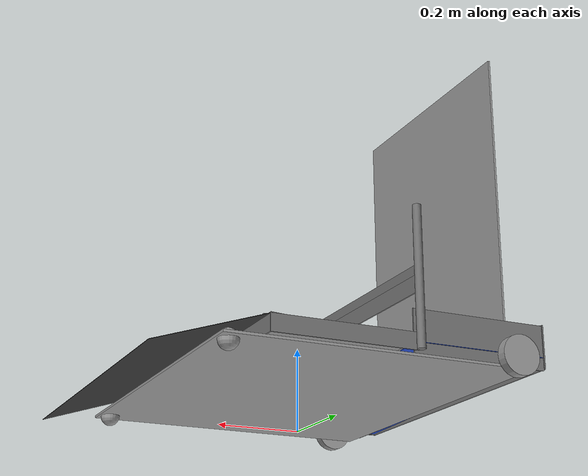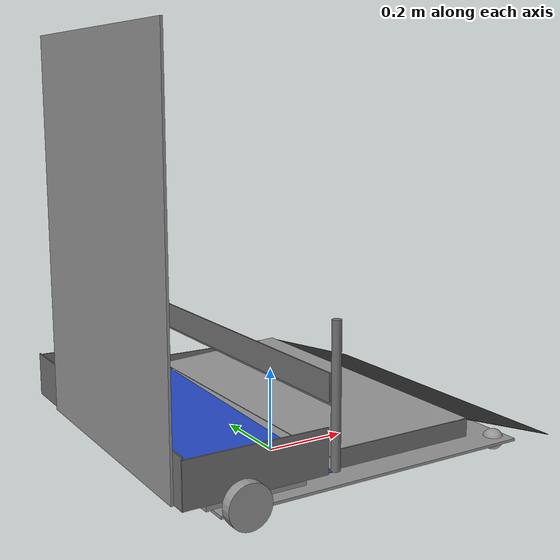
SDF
<?xml version='1.0'?>
<sdf version='1.6'>
  <model name='blue_3'>

    <include>
      <uri>model://frc_blue_scorer</uri>
    </include>

    <plugin name='diff_drive' filename='libFRCBlueDiffDrivePlugin.so'>
      <topic>/blue/joy3</topic>
      <torque>-60</torque>
      <turn_rate>1.0</turn_rate>
      <left_joint>frc2016_blue_scorer::wheel_1_JOINT</left_joint>
      <right_joint>frc2016_blue_scorer::wheel_2_JOINT</right_joint>
    </plugin>

    <plugin name='FRCBlueScorerPlugin' filename='libFRCBlueScorerPlugin.so'>

      <topic>/blue/joy3</topic>
      <joint>
        <name>frc2016_blue_scorer::collector_gate</name>
        <lower_limit>0</lower_limit>
        <upper_limit>0.6</upper_limit>
        <button_index>0</button_index>
        <p_gain>10</p_gain>
        <d_gain>0</d_gain>
      </joint>

      <joint>
        <name>frc2016_blue_scorer::pocket_gate</name>
        <lower_limit>0</lower_limit>
        <upper_limit>0.6</upper_limit>
        <button_index>1</button_index>
        <p_gain>15</p_gain>
        <d_gain>0</d_gain>
      </joint>

      <joint>
        <name>frc2016_blue_scorer::elevator_beam_lift</name>
        <lower_limit>0</lower_limit>
        <upper_limit>1.11</upper_limit>
        <button_index>3</button_index>
        <p_gain>500</p_gain>
        <d_gain>200</d_gain>
      </joint>

      <joint>
        <name>frc2016_blue_scorer::elevator_beam_lift_2</name>
        <lower_limit>0</lower_limit>
        <upper_limit>1.11</upper_limit>
        <button_index>3</button_index>
        <p_gain>400</p_gain>
        <d_gain>200</d_gain>
      </joint>

      <joint>
        <name>frc2016_blue_scorer::elevator_beam_lift_3</name>
        <lower_limit>0</lower_limit>
        <upper_limit>1.11</upper_limit>
        <button_index>3</button_index>
        <p_gain>300</p_gain>
        <d_gain>200</d_gain>
      </joint>

      <joint>
        <name>frc2016_blue_scorer::pocket_slider</name>
        <lower_limit>0</lower_limit>
        <upper_limit>1.05</upper_limit>
        <button_index>2</button_index>
        <p_gain>100</p_gain>
        <d_gain>0</d_gain>
      </joint>

      <joint>
        <name>frc2016_blue_scorer::score_gate</name>
        <lower_limit>0</lower_limit>
        <upper_limit>1.6</upper_limit>
        <button_index>7</button_index>
        <p_gain>10</p_gain>
        <d_gain>0</d_gain>
      </joint>

    </plugin>
  </model>
</sdf>

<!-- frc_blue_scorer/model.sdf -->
<sdf version='1.6'>
  <model name='frc2016_blue_scorer'>
    <link name='collector_plate'>
      <pose frame=''>0.077308 0 0.141077 0 -0.062752 0</pose>
      <inertial>
        <mass>1.20648</mass>
        <pose frame=''>0 0 0 0 -0 0</pose>
        <inertia>
          <ixx>0.0643458</ixx>
          <ixy>0</ixy>
          <ixz>0</ixz>
          <iyy>0.0117771</iyy>
          <iyz>0</iyz>
          <izz>0.0761223</izz>
        </inertia>
      </inertial>
      <self_collide>0</self_collide>
      <enable_wind>0</enable_wind>
      <kinematic>0</kinematic>
      <gravity>1</gravity>
      <visual name='platform'>
        <geometry>
          <box>
            <size>0.342252 0.8 0.001632</size>
          </box>
        </geometry>
        <pose frame=''>0 0 0 0 -0 0</pose>
        <cast_shadows>1</cast_shadows>
        <transparency>0</transparency>
        <material>
          <lighting>1</lighting>
          <script>
            <uri>file://media/materials/scripts/gazebo.material</uri>
            <name>Gazebo/Grey</name>
          </script>
          <ambient>0.2 0.2 0.2 1</ambient>
          <diffuse>0.2 0.2 0.2 1</diffuse>
          <specular>0.2 0.2 0.2 1</specular>
          <emissive>0.2 0.2 0.2 1</emissive>
          <shader type='vertex'>
            <normal_map>__default__</normal_map>
          </shader>
        </material>
      </visual>
      <collision name='platform'>
        <laser_retro>0</laser_retro>
        <max_contacts>10</max_contacts>
        <pose frame=''>0 0 0 0 -0 0</pose>
        <geometry>
          <box>
            <size>0.342252 0.8 0.001632</size>
          </box>
        </geometry>
        <surface>
          <friction>
            <ode>
              <mu>1</mu>
              <mu2>1</mu2>
              <fdir1>0 0 0</fdir1>
              <slip1>0</slip1>
              <slip2>0</slip2>
            </ode>
            <torsional>
              <coefficient>1</coefficient>
              <patch_radius>0</patch_radius>
              <surface_radius>0</surface_radius>
              <use_patch_radius>1</use_patch_radius>
              <ode>
                <slip>0</slip>
              </ode>
            </torsional>
          </friction>
          <bounce>
            <restitution_coefficient>0</restitution_coefficient>
            <threshold>1e+06</threshold>
          </bounce>
          <contact>
            <collide_without_contact>0</collide_without_contact>
            <collide_without_contact_bitmask>1</collide_without_contact_bitmask>
            <collide_bitmask>1</collide_bitmask>
            <ode>
              <soft_cfm>0</soft_cfm>
              <soft_erp>0.2</soft_erp>
              <kp>1e+08</kp>
              <kd>1</kd>
              <max_vel>1000</max_vel>
              <min_depth>0.01</min_depth>
            </ode>
            <bullet>
              <split_impulse>1</split_impulse>
              <split_impulse_penetration_threshold>-0.01</split_impulse_penetration_threshold>
              <soft_cfm>0</soft_cfm>
              <soft_erp>0.2</soft_erp>
              <kp>1e+08</kp>
              <kd>1</kd>
            </bullet>
          </contact>
        </surface>
      </collision>
    </link>
    <link name='base'>
      <inertial>
        <mass>10.2329</mass>
        <inertia>
          <ixx>0.637039</ixx>
          <ixy>0</ixy>
          <ixz>0</ixz>
          <iyy>0.455502</iyy>
          <iyz>0</iyz>
          <izz>1.09248</izz>
        </inertia>
        <pose frame=''>0 0 0 0 -0 0</pose>
      </inertial>
      <pose frame=''>-0 0 0.09 -1e-06 -0 -5e-06</pose>
      <gravity>1</gravity>
      <self_collide>0</self_collide>
      <kinematic>0</kinematic>
      <enable_wind>0</enable_wind>
      <visual name='visual_base'>
        <pose frame=''>0 0 0 0 -0 0</pose>
        <geometry>
          <box>
            <size>0.730838 0.864298 0.006</size>
          </box>
        </geometry>
        <material>
          <lighting>1</lighting>
          <script>
            <uri>file://media/materials/scripts/gazebo.material</uri>
            <name>Gazebo/Grey</name>
          </script>
          <ambient>0.3 0.3 0.3 1</ambient>
          <diffuse>0.7 0.7 0.7 1</diffuse>
          <specular>0.01 0.01 0.01 1</specular>
          <emissive>0 0 0 1</emissive>
          <shader type='vertex'>
            <normal_map>__default__</normal_map>
          </shader>
        </material>
        <cast_shadows>1</cast_shadows>
        <transparency>0</transparency>
      </visual>
      <visual name='visual_caster_2'>
        <pose frame=''>0.338156 0.392417 -0.005 0 -0 0</pose>
        <geometry>
          <sphere>
            <radius>0.023419</radius>
          </sphere>
        </geometry>
        <material>
          <lighting>1</lighting>
          <script>
            <uri>file://media/materials/scripts/gazebo.material</uri>
            <name>Gazebo/Grey</name>
          </script>
          <ambient>0.3 0.3 0.3 1</ambient>
          <diffuse>0.7 0.7 0.7 1</diffuse>
          <specular>0.01 0.01 0.01 1</specular>
          <emissive>0 0 0 1</emissive>
          <shader type='pixel'>
            <normal_map>__default__</normal_map>
          </shader>
        </material>
        <cast_shadows>1</cast_shadows>
        <transparency>0</transparency>
      </visual>
      <visual name='visual_caster_1'>
        <pose frame=''>0.338156 -0.392417 -0.005 0 -0 0</pose>
        <geometry>
          <sphere>
            <radius>0.023419</radius>
          </sphere>
        </geometry>
        <material>
          <lighting>1</lighting>
          <script>
            <uri>file://media/materials/scripts/gazebo.material</uri>
            <name>Gazebo/Grey</name>
          </script>
          <ambient>0.3 0.3 0.3 1</ambient>
          <diffuse>0.7 0.7 0.7 1</diffuse>
          <specular>0.01 0.01 0.01 1</specular>
          <emissive>0 0 0 1</emissive>
          <shader type='pixel'>
            <normal_map>__default__</normal_map>
          </shader>
        </material>
        <cast_shadows>1</cast_shadows>
        <transparency>0</transparency>
      </visual>
      <collision name='collision_caster_1'>
        <laser_retro>0</laser_retro>
        <max_contacts>10</max_contacts>
        <pose frame=''>0.338156 -0.392417 -0.005 0 -0 0</pose>
        <geometry>
          <sphere>
            <radius>0.023419</radius>
          </sphere>
        </geometry>
        <surface>
          <friction>
            <ode>
              <mu>0</mu>
              <mu2>0</mu2>
              <fdir1>0 0 0</fdir1>
              <slip1>0</slip1>
              <slip2>0</slip2>
            </ode>
            <torsional>
              <coefficient>1</coefficient>
              <patch_radius>0</patch_radius>
              <surface_radius>0</surface_radius>
              <use_patch_radius>1</use_patch_radius>
              <ode>
                <slip>0</slip>
              </ode>
            </torsional>
          </friction>
          <bounce>
            <restitution_coefficient>0</restitution_coefficient>
            <threshold>1e+06</threshold>
          </bounce>
          <contact>
            <collide_without_contact>0</collide_without_contact>
            <collide_without_contact_bitmask>1</collide_without_contact_bitmask>
            <collide_bitmask>1</collide_bitmask>
            <ode>
              <kp>1e+6</kp>
              <kd>1</kd>
              <max_vel>100.0</max_vel>
              <min_depth>0.002</min_depth>
            </ode>
            <bullet>
              <split_impulse>1</split_impulse>
              <split_impulse_penetration_threshold>-0.01</split_impulse_penetration_threshold>
              <soft_cfm>0</soft_cfm>
              <soft_erp>0.2</soft_erp>
              <kp>1e+13</kp>
              <kd>1</kd>
            </bullet>
          </contact>
        </surface>
      </collision>
      <collision name='collision_caster_2'>
        <laser_retro>0</laser_retro>
        <max_contacts>10</max_contacts>
        <pose frame=''>0.338156 0.392417 -0.005 0 -0 0</pose>
        <geometry>
          <sphere>
            <radius>0.023419</radius>
          </sphere>
        </geometry>
        <surface>
          <friction>
            <ode>
              <mu>0</mu>
              <mu2>0</mu2>
              <fdir1>0 0 0</fdir1>
              <slip1>0</slip1>
              <slip2>0</slip2>
            </ode>
            <torsional>
              <coefficient>1</coefficient>
              <patch_radius>0</patch_radius>
              <surface_radius>0</surface_radius>
              <use_patch_radius>1</use_patch_radius>
              <ode>
                <slip>0</slip>
              </ode>
            </torsional>
          </friction>
          <bounce>
            <restitution_coefficient>0</restitution_coefficient>
            <threshold>1e+06</threshold>
          </bounce>
          <contact>
            <collide_without_contact>0</collide_without_contact>
            <collide_without_contact_bitmask>1</collide_without_contact_bitmask>
            <collide_bitmask>1</collide_bitmask>
            <ode>
              <kp>1e+6</kp>
              <kd>1</kd>
              <max_vel>100.0</max_vel>
              <min_depth>0.002</min_depth>
            </ode>
            <bullet>
              <split_impulse>1</split_impulse>
              <split_impulse_penetration_threshold>-0.01</split_impulse_penetration_threshold>
              <soft_cfm>0</soft_cfm>
              <soft_erp>0.2</soft_erp>
              <kp>1e+13</kp>
              <kd>1</kd>
            </bullet>
          </contact>
        </surface>
      </collision>
      <collision name='collision_base'>
        <laser_retro>0</laser_retro>
        <max_contacts>10</max_contacts>
        <pose frame=''>0 0 0 0 -0 0</pose>
        <geometry>
          <box>
            <size>0.730838 0.864298 0.006</size>
          </box>
        </geometry>
        <surface>
          <friction>
            <ode>
              <mu>1</mu>
              <mu2>1</mu2>
              <fdir1>0 0 0</fdir1>
              <slip1>0</slip1>
              <slip2>0</slip2>
            </ode>
            <torsional>
              <coefficient>1</coefficient>
              <patch_radius>0</patch_radius>
              <surface_radius>0</surface_radius>
              <use_patch_radius>1</use_patch_radius>
              <ode>
                <slip>0</slip>
              </ode>
            </torsional>
          </friction>
          <bounce>
            <restitution_coefficient>0</restitution_coefficient>
            <threshold>1e+06</threshold>
          </bounce>
          <contact>
            <collide_without_contact>0</collide_without_contact>
            <collide_without_contact_bitmask>1</collide_without_contact_bitmask>
            <collide_bitmask>1</collide_bitmask>
            <ode>
              <soft_cfm>0</soft_cfm>
              <soft_erp>0.2</soft_erp>
              <kp>1e+13</kp>
              <kd>1</kd>
              <max_vel>0.01</max_vel>
              <min_depth>0</min_depth>
            </ode>
            <bullet>
              <split_impulse>1</split_impulse>
              <split_impulse_penetration_threshold>-0.01</split_impulse_penetration_threshold>
              <soft_cfm>0</soft_cfm>
              <soft_erp>0.2</soft_erp>
              <kp>1e+13</kp>
              <kd>1</kd>
            </bullet>
          </contact>
        </surface>
      </collision>
    </link>
    <link name='pocket_beam_left'>
      <pose frame=''>-0.1 -0.41 0.265004 0 -0 0</pose>
      <inertial>
        <mass>2.56966</mass>
        <pose frame=''>0 0 0 0 -0 0</pose>
        <inertia>
          <ixx>0.0197171</ixx>
          <ixy>0</ixy>
          <ixz>0</ixz>
          <iyy>0.0197171</iyy>
          <iyz>0</iyz>
          <izz>0.000128448</izz>
        </inertia>
      </inertial>
      <self_collide>0</self_collide>
      <enable_wind>0</enable_wind>
      <kinematic>0</kinematic>
      <gravity>1</gravity>
      <visual name='beam_left'>
        <geometry>
          <cylinder>
            <radius>0.01</radius>
            <length>0.302943</length>
          </cylinder>
        </geometry>
        <material>
          <ambient>0.46 0.46 0.46 1</ambient>
          <diffuse>0.46 0.46 0.46 1</diffuse>
          <specular>0 0 0 1</specular>
          <emissive>0 0 0 1</emissive>
          <script>
            <name>ModelPreview_1::beam_left::beam_left_MATERIAL_</name>
            <uri>__default__</uri>
          </script>
          <shader type='vertex'>
            <normal_map>__default__</normal_map>
          </shader>
        </material>
        <pose frame=''>0 0 0 0 -0 0</pose>
        <cast_shadows>1</cast_shadows>
        <transparency>0</transparency>
      </visual>
      <collision name='beam_left'>
        <laser_retro>0</laser_retro>
        <max_contacts>10</max_contacts>
        <pose frame=''>0 0 0 0 -0 0</pose>
        <geometry>
          <cylinder>
            <radius>0.01</radius>
            <length>0.302943</length>
          </cylinder>
        </geometry>
        <surface>
          <friction>
            <ode>
              <mu>1</mu>
              <mu2>1</mu2>
              <fdir1>0 0 0</fdir1>
              <slip1>0</slip1>
              <slip2>0</slip2>
            </ode>
            <torsional>
              <coefficient>1</coefficient>
              <patch_radius>0</patch_radius>
              <surface_radius>0</surface_radius>
              <use_patch_radius>1</use_patch_radius>
              <ode>
                <slip>0</slip>
              </ode>
            </torsional>
          </friction>
          <bounce>
            <restitution_coefficient>0</restitution_coefficient>
            <threshold>1e+06</threshold>
          </bounce>
          <contact>
            <collide_without_contact>0</collide_without_contact>
            <collide_without_contact_bitmask>1</collide_without_contact_bitmask>
            <collide_bitmask>1</collide_bitmask>
            <ode>
              <soft_cfm>0</soft_cfm>
              <soft_erp>0.2</soft_erp>
              <kp>1e+08</kp>
              <kd>1</kd>
              <max_vel>1000</max_vel>
              <min_depth>0.01</min_depth>
            </ode>
            <bullet>
              <split_impulse>1</split_impulse>
              <split_impulse_penetration_threshold>-0.01</split_impulse_penetration_threshold>
              <soft_cfm>0</soft_cfm>
              <soft_erp>0.2</soft_erp>
              <kp>1e+08</kp>
              <kd>1</kd>
            </bullet>
          </contact>
        </surface>
      </collision>
    </link>
    <link name='pocket_beam_right'>
      <pose frame=''>-0.1 0.41 0.275744 0 -0 0</pose>
      <inertial>
        <mass>2.80084</mass>
        <pose frame=''>0 0 0 0 -0 0</pose>
        <inertia>
          <ixx>0.0255185</ixx>
          <ixy>0</ixy>
          <ixz>0</ixz>
          <iyy>0.0255185</iyy>
          <iyz>0</iyz>
          <izz>0.000140004</izz>
        </inertia>
      </inertial>
      <self_collide>0</self_collide>
      <enable_wind>0</enable_wind>
      <kinematic>0</kinematic>
      <gravity>1</gravity>
      <visual name='beam_right'>
        <geometry>
          <cylinder>
            <radius>0.01</radius>
            <length>0.330197</length>
          </cylinder>
        </geometry>
        <material>
          <ambient>0.46 0.46 0.46 1</ambient>
          <diffuse>0.46 0.46 0.46 1</diffuse>
          <specular>0 0 0 1</specular>
          <emissive>0 0 0 1</emissive>
          <script>
            <name>ModelPreview_1::beam_right::beam_right_MATERIAL_</name>
            <uri>__default__</uri>
          </script>
          <shader type='vertex'>
            <normal_map>__default__</normal_map>
          </shader>
        </material>
        <pose frame=''>0 0 0 0 -0 0</pose>
        <cast_shadows>1</cast_shadows>
        <transparency>0</transparency>
      </visual>
      <collision name='beam_right'>
        <laser_retro>0</laser_retro>
        <max_contacts>10</max_contacts>
        <pose frame=''>0 0 0 0 -0 0</pose>
        <geometry>
          <cylinder>
            <radius>0.01</radius>
            <length>0.330197</length>
          </cylinder>
        </geometry>
        <surface>
          <friction>
            <ode>
              <mu>1</mu>
              <mu2>1</mu2>
              <fdir1>0 0 0</fdir1>
              <slip1>0</slip1>
              <slip2>0</slip2>
            </ode>
            <torsional>
              <coefficient>1</coefficient>
              <patch_radius>0</patch_radius>
              <surface_radius>0</surface_radius>
              <use_patch_radius>1</use_patch_radius>
              <ode>
                <slip>0</slip>
              </ode>
            </torsional>
          </friction>
          <bounce>
            <restitution_coefficient>0</restitution_coefficient>
            <threshold>1e+06</threshold>
          </bounce>
          <contact>
            <collide_without_contact>0</collide_without_contact>
            <collide_without_contact_bitmask>1</collide_without_contact_bitmask>
            <collide_bitmask>1</collide_bitmask>
            <ode>
              <soft_cfm>0</soft_cfm>
              <soft_erp>0.2</soft_erp>
              <kp>1e+08</kp>
              <kd>1</kd>
              <max_vel>1000</max_vel>
              <min_depth>0.01</min_depth>
            </ode>
            <bullet>
              <split_impulse>1</split_impulse>
              <split_impulse_penetration_threshold>-0.01</split_impulse_penetration_threshold>
              <soft_cfm>0</soft_cfm>
              <soft_erp>0.2</soft_erp>
              <kp>1e+08</kp>
              <kd>1</kd>
            </bullet>
          </contact>
        </surface>
      </collision>
    </link>
    <link name='beam_left'>
      <pose frame=''>-0.1 -0.41 0.265004 0 -0 0</pose>
      <inertial>
        <mass>2.56966</mass>
        <pose frame=''>0 0 0 0 -0 0</pose>
        <inertia>
          <ixx>0.0197171</ixx>
          <ixy>0</ixy>
          <ixz>0</ixz>
          <iyy>0.0197171</iyy>
          <iyz>0</iyz>
          <izz>0.000128448</izz>
        </inertia>
      </inertial>
      <self_collide>0</self_collide>
      <enable_wind>0</enable_wind>
      <kinematic>0</kinematic>
      <gravity>1</gravity>
      <visual name='beam_left'>
        <geometry>
          <cylinder>
            <radius>0.01</radius>
            <length>0.302943</length>
          </cylinder>
        </geometry>
        <material>
          <ambient>0.46 0.46 0.46 1</ambient>
          <diffuse>0.46 0.46 0.46 1</diffuse>
          <specular>0 0 0 1</specular>
          <emissive>0 0 0 1</emissive>
          <script>
            <name>ModelPreview_1::beam_left::beam_left_MATERIAL_</name>
            <uri>__default__</uri>
          </script>
          <shader type='vertex'>
            <normal_map>__default__</normal_map>
          </shader>
        </material>
        <pose frame=''>0 0 0 0 -0 0</pose>
        <cast_shadows>1</cast_shadows>
        <transparency>0</transparency>
      </visual>
      <collision name='beam_left'>
        <laser_retro>0</laser_retro>
        <max_contacts>10</max_contacts>
        <pose frame=''>0 0 0 0 -0 0</pose>
        <geometry>
          <cylinder>
            <radius>0.01</radius>
            <length>0.302943</length>
          </cylinder>
        </geometry>
        <surface>
          <friction>
            <ode>
              <mu>1</mu>
              <mu2>1</mu2>
              <fdir1>0 0 0</fdir1>
              <slip1>0</slip1>
              <slip2>0</slip2>
            </ode>
            <torsional>
              <coefficient>1</coefficient>
              <patch_radius>0</patch_radius>
              <surface_radius>0</surface_radius>
              <use_patch_radius>1</use_patch_radius>
              <ode>
                <slip>0</slip>
              </ode>
            </torsional>
          </friction>
          <bounce>
            <restitution_coefficient>0</restitution_coefficient>
            <threshold>1e+06</threshold>
          </bounce>
          <contact>
            <collide_without_contact>0</collide_without_contact>
            <collide_without_contact_bitmask>1</collide_without_contact_bitmask>
            <collide_bitmask>1</collide_bitmask>
            <ode>
              <soft_cfm>0</soft_cfm>
              <soft_erp>0.2</soft_erp>
              <kp>1e+08</kp>
              <kd>1</kd>
              <max_vel>1000</max_vel>
              <min_depth>0.01</min_depth>
            </ode>
            <bullet>
              <split_impulse>1</split_impulse>
              <split_impulse_penetration_threshold>-0.01</split_impulse_penetration_threshold>
              <soft_cfm>0</soft_cfm>
              <soft_erp>0.2</soft_erp>
              <kp>1e+08</kp>
              <kd>1</kd>
            </bullet>
          </contact>
        </surface>
      </collision>
    </link>
    <link name='beam_right'>
      <pose frame=''>-0.1 0.41 0.275744 0 -0 0</pose>
      <inertial>
        <mass>2.80084</mass>
        <pose frame=''>0 0 0 0 -0 0</pose>
        <inertia>
          <ixx>0.0255185</ixx>
          <ixy>0</ixy>
          <ixz>0</ixz>
          <iyy>0.0255185</iyy>
          <iyz>0</iyz>
          <izz>0.000140004</izz>
        </inertia>
      </inertial>
      <self_collide>0</self_collide>
      <enable_wind>0</enable_wind>
      <kinematic>0</kinematic>
      <gravity>1</gravity>
      <visual name='beam_right'>
        <geometry>
          <cylinder>
            <radius>0.01</radius>
            <length>0.330197</length>
          </cylinder>
        </geometry>
        <material>
          <ambient>0.46 0.46 0.46 1</ambient>
          <diffuse>0.46 0.46 0.46 1</diffuse>
          <specular>0 0 0 1</specular>
          <emissive>0 0 0 1</emissive>
          <script>
            <name>ModelPreview_1::beam_right::beam_right_MATERIAL_</name>
            <uri>__default__</uri>
          </script>
          <shader type='vertex'>
            <normal_map>__default__</normal_map>
          </shader>
        </material>
        <pose frame=''>0 0 0 0 -0 0</pose>
        <cast_shadows>1</cast_shadows>
        <transparency>0</transparency>
      </visual>
      <collision name='beam_right'>
        <laser_retro>0</laser_retro>
        <max_contacts>10</max_contacts>
        <pose frame=''>0 0 0 0 -0 0</pose>
        <geometry>
          <cylinder>
            <radius>0.01</radius>
            <length>0.330197</length>
          </cylinder>
        </geometry>
        <surface>
          <friction>
            <ode>
              <mu>1</mu>
              <mu2>1</mu2>
              <fdir1>0 0 0</fdir1>
              <slip1>0</slip1>
              <slip2>0</slip2>
            </ode>
            <torsional>
              <coefficient>1</coefficient>
              <patch_radius>0</patch_radius>
              <surface_radius>0</surface_radius>
              <use_patch_radius>1</use_patch_radius>
              <ode>
                <slip>0</slip>
              </ode>
            </torsional>
          </friction>
          <bounce>
            <restitution_coefficient>0</restitution_coefficient>
            <threshold>1e+06</threshold>
          </bounce>
          <contact>
            <collide_without_contact>0</collide_without_contact>
            <collide_without_contact_bitmask>1</collide_without_contact_bitmask>
            <collide_bitmask>1</collide_bitmask>
            <ode>
              <soft_cfm>0</soft_cfm>
              <soft_erp>0.2</soft_erp>
              <kp>1e+08</kp>
              <kd>1</kd>
              <max_vel>1000</max_vel>
              <min_depth>0.01</min_depth>
            </ode>
            <bullet>
              <split_impulse>1</split_impulse>
              <split_impulse_penetration_threshold>-0.01</split_impulse_penetration_threshold>
              <soft_cfm>0</soft_cfm>
              <soft_erp>0.2</soft_erp>
              <kp>1e+08</kp>
              <kd>1</kd>
            </bullet>
          </contact>
        </surface>
      </collision>
    </link>
    <link name='elevator_beam'>
      <inertial>
        <mass>5.6408</mass>
        <inertia>
          <ixx>0.378279</ixx>
          <ixy>0</ixy>
          <ixz>0</ixz>
          <iyy>0.198061</iyy>
          <iyz>0</iyz>
          <izz>0.180243</izz>
        </inertia>
        <pose frame=''>0 0 0 0 -0 0</pose>
      </inertial>
      <pose frame=''>-0.44053 -0.079637 0.538197 0 -0 0</pose>
      <gravity>1</gravity>
      <self_collide>0</self_collide>
      <kinematic>0</kinematic>
      <enable_wind>0</enable_wind>
      <visual name='visual'>
        <pose frame=''>0 0 0 0 -0 0</pose>
        <geometry>
          <box>
            <size>0.005198 0.619205 0.849092</size>
          </box>
        </geometry>
        <material>
          <lighting>1</lighting>
          <script>
            <uri>file://media/materials/scripts/gazebo.material</uri>
            <name>Gazebo/Grey</name>
          </script>
          <ambient>0.3 0.3 0.3 1</ambient>
          <diffuse>0.7 0.7 0.7 1</diffuse>
          <specular>0.01 0.01 0.01 1</specular>
          <emissive>0 0 0 1</emissive>
          <shader type='vertex'>
            <normal_map>__default__</normal_map>
          </shader>
        </material>
        <cast_shadows>1</cast_shadows>
        <transparency>0</transparency>
      </visual>
      <collision name='collision'>
        <laser_retro>0</laser_retro>
        <max_contacts>10</max_contacts>
        <pose frame=''>0 0 0 0 -0 0</pose>
        <geometry>
          <box>
            <size>0.005198 0.619205 0.849092</size>
          </box>
        </geometry>
        <surface>
          <friction>
            <ode>
              <mu>1</mu>
              <mu2>1</mu2>
              <fdir1>0 0 0</fdir1>
              <slip1>0</slip1>
              <slip2>0</slip2>
            </ode>
            <torsional>
              <coefficient>1</coefficient>
              <patch_radius>0</patch_radius>
              <surface_radius>0</surface_radius>
              <use_patch_radius>1</use_patch_radius>
              <ode>
                <slip>0</slip>
              </ode>
            </torsional>
          </friction>
          <bounce>
            <restitution_coefficient>0</restitution_coefficient>
            <threshold>1e+06</threshold>
          </bounce>
          <contact>
            <collide_without_contact>0</collide_without_contact>
            <collide_without_contact_bitmask>1</collide_without_contact_bitmask>
            <collide_bitmask>1</collide_bitmask>
            <ode>
              <soft_cfm>0</soft_cfm>
              <soft_erp>0.2</soft_erp>
              <kp>1e+13</kp>
              <kd>1</kd>
              <max_vel>0.01</max_vel>
              <min_depth>0</min_depth>
            </ode>
            <bullet>
              <split_impulse>1</split_impulse>
              <split_impulse_penetration_threshold>-0.01</split_impulse_penetration_threshold>
              <soft_cfm>0</soft_cfm>
              <soft_erp>0.2</soft_erp>
              <kp>1e+13</kp>
              <kd>1</kd>
            </bullet>
          </contact>
        </surface>
      </collision>
    </link>
    <link name='elevator_beam_1'>
      <inertial>
        <mass>5.6408</mass>
        <inertia>
          <ixx>0.378279</ixx>
          <ixy>0</ixy>
          <ixz>0</ixz>
          <iyy>0.198061</iyy>
          <iyz>0</iyz>
          <izz>0.180243</izz>
        </inertia>
        <pose frame=''>0 0 0 0 -0 0</pose>
      </inertial>
      <pose frame=''>-0.44053 -0.079637 0.538197 0 -0 0</pose>
      <gravity>1</gravity>
      <self_collide>0</self_collide>
      <kinematic>0</kinematic>
      <enable_wind>0</enable_wind>
      <visual name='visual'>
        <pose frame=''>0 0 0 0 -0 0</pose>
        <geometry>
          <box>
            <size>0.005198 0.619205 0.849092</size>
          </box>
        </geometry>
        <material>
          <lighting>1</lighting>
          <script>
            <uri>file://media/materials/scripts/gazebo.material</uri>
            <name>Gazebo/Grey</name>
          </script>
          <ambient>0.3 0.3 0.3 1</ambient>
          <diffuse>0.7 0.7 0.7 1</diffuse>
          <specular>0.01 0.01 0.01 1</specular>
          <emissive>0 0 0 1</emissive>
          <shader type='vertex'>
            <normal_map>__default__</normal_map>
          </shader>
        </material>
        <cast_shadows>1</cast_shadows>
        <transparency>0</transparency>
      </visual>
      <collision name='collision'>
        <laser_retro>0</laser_retro>
        <max_contacts>10</max_contacts>
        <pose frame=''>0 0 0 0 -0 0</pose>
        <geometry>
          <box>
            <size>0.005198 0.619205 0.849092</size>
          </box>
        </geometry>
        <surface>
          <friction>
            <ode>
              <mu>1</mu>
              <mu2>1</mu2>
              <fdir1>0 0 0</fdir1>
              <slip1>0</slip1>
              <slip2>0</slip2>
            </ode>
            <torsional>
              <coefficient>1</coefficient>
              <patch_radius>0</patch_radius>
              <surface_radius>0</surface_radius>
              <use_patch_radius>1</use_patch_radius>
              <ode>
                <slip>0</slip>
              </ode>
            </torsional>
          </friction>
          <bounce>
            <restitution_coefficient>0</restitution_coefficient>
            <threshold>1e+06</threshold>
          </bounce>
          <contact>
            <collide_without_contact>0</collide_without_contact>
            <collide_without_contact_bitmask>1</collide_without_contact_bitmask>
            <collide_bitmask>1</collide_bitmask>
            <ode>
              <soft_cfm>0</soft_cfm>
              <soft_erp>0.2</soft_erp>
              <kp>1e+13</kp>
              <kd>1</kd>
              <max_vel>0.01</max_vel>
              <min_depth>0</min_depth>
            </ode>
            <bullet>
              <split_impulse>1</split_impulse>
              <split_impulse_penetration_threshold>-0.01</split_impulse_penetration_threshold>
              <soft_cfm>0</soft_cfm>
              <soft_erp>0.2</soft_erp>
              <kp>1e+13</kp>
              <kd>1</kd>
            </bullet>
          </contact>
        </surface>
      </collision>
    </link>
    <link name='elevator_beam_2'>
      <inertial>
        <mass>5.6408</mass>
        <inertia>
          <ixx>0.378279</ixx>
          <ixy>0</ixy>
          <ixz>0</ixz>
          <iyy>0.198061</iyy>
          <iyz>0</iyz>
          <izz>0.180243</izz>
        </inertia>
        <pose frame=''>0 0 0 0 -0 0</pose>
      </inertial>
      <pose frame=''>-0.44053 -0.079637 0.538197 0 -0 0</pose>
      <gravity>1</gravity>
      <self_collide>0</self_collide>
      <kinematic>0</kinematic>
      <enable_wind>0</enable_wind>
      <visual name='visual'>
        <pose frame=''>0 0 0 0 -0 0</pose>
        <geometry>
          <box>
            <size>0.005198 0.619205 0.849092</size>
          </box>
        </geometry>
        <material>
          <lighting>1</lighting>
          <script>
            <uri>file://media/materials/scripts/gazebo.material</uri>
            <name>Gazebo/Grey</name>
          </script>
          <ambient>0.3 0.3 0.3 1</ambient>
          <diffuse>0.7 0.7 0.7 1</diffuse>
          <specular>0.01 0.01 0.01 1</specular>
          <emissive>0 0 0 1</emissive>
          <shader type='vertex'>
            <normal_map>__default__</normal_map>
          </shader>
        </material>
        <cast_shadows>1</cast_shadows>
        <transparency>0</transparency>
      </visual>
      <collision name='collision'>
        <laser_retro>0</laser_retro>
        <max_contacts>10</max_contacts>
        <pose frame=''>0 0 0 0 -0 0</pose>
        <geometry>
          <box>
            <size>0.005198 0.619205 0.849092</size>
          </box>
        </geometry>
        <surface>
          <friction>
            <ode>
              <mu>1</mu>
              <mu2>1</mu2>
              <fdir1>0 0 0</fdir1>
              <slip1>0</slip1>
              <slip2>0</slip2>
            </ode>
            <torsional>
              <coefficient>1</coefficient>
              <patch_radius>0</patch_radius>
              <surface_radius>0</surface_radius>
              <use_patch_radius>1</use_patch_radius>
              <ode>
                <slip>0</slip>
              </ode>
            </torsional>
          </friction>
          <bounce>
            <restitution_coefficient>0</restitution_coefficient>
            <threshold>1e+06</threshold>
          </bounce>
          <contact>
            <collide_without_contact>0</collide_without_contact>
            <collide_without_contact_bitmask>1</collide_without_contact_bitmask>
            <collide_bitmask>1</collide_bitmask>
            <ode>
              <soft_cfm>0</soft_cfm>
              <soft_erp>0.2</soft_erp>
              <kp>1e+13</kp>
              <kd>1</kd>
              <max_vel>0.01</max_vel>
              <min_depth>0</min_depth>
            </ode>
            <bullet>
              <split_impulse>1</split_impulse>
              <split_impulse_penetration_threshold>-0.01</split_impulse_penetration_threshold>
              <soft_cfm>0</soft_cfm>
              <soft_erp>0.2</soft_erp>
              <kp>1e+13</kp>
              <kd>1</kd>
            </bullet>
          </contact>
        </surface>
      </collision>
    </link>
    <link name='platform_side1'>
      <pose frame=''>0.075 -0.4 0.13105 0 -0 0</pose>
      <inertial>
        <mass>0.120015</mass>
        <pose frame=''>0 0 0 0 -0 0</pose>
        <inertia>
          <ixx>1.61e-05</ixx>
          <ixy>0</ixy>
          <ixz>0</ixz>
          <iyy>0.00124116</iyy>
          <iyz>0</iyz>
          <izz>0.00122525</izz>
        </inertia>
      </inertial>
      <self_collide>0</self_collide>
      <enable_wind>0</enable_wind>
      <kinematic>0</kinematic>
      <gravity>1</gravity>
      <visual name='platform_side1'>
        <geometry>
          <box>
            <size>0.35 0.003175 0.04</size>
          </box>
        </geometry>
        <material>
          <ambient>0.46 0.46 0.46 1</ambient>
          <diffuse>0.46 0.46 0.46 1</diffuse>
          <specular>0 0 0 1</specular>
          <emissive>0 0 0 1</emissive>
          <script>
            <name>ModelPreview_1::platform_side1::platform_side1_MATERIAL_</name>
            <uri>__default__</uri>
          </script>
          <shader type='vertex'>
            <normal_map>__default__</normal_map>
          </shader>
        </material>
        <pose frame=''>0 0 0 0 -0 0</pose>
        <cast_shadows>1</cast_shadows>
        <transparency>0</transparency>
      </visual>
      <collision name='platform_side1'>
        <laser_retro>0</laser_retro>
        <max_contacts>10</max_contacts>
        <pose frame=''>0 0 0 0 -0 0</pose>
        <geometry>
          <box>
            <size>0.35 0.003175 0.04</size>
          </box>
        </geometry>
        <surface>
          <friction>
            <ode>
              <mu>1</mu>
              <mu2>1</mu2>
              <fdir1>0 0 0</fdir1>
              <slip1>0</slip1>
              <slip2>0</slip2>
            </ode>
            <torsional>
              <coefficient>1</coefficient>
              <patch_radius>0</patch_radius>
              <surface_radius>0</surface_radius>
              <use_patch_radius>1</use_patch_radius>
              <ode>
                <slip>0</slip>
              </ode>
            </torsional>
          </friction>
          <bounce>
            <restitution_coefficient>0</restitution_coefficient>
            <threshold>1e+06</threshold>
          </bounce>
          <contact>
            <collide_without_contact>0</collide_without_contact>
            <collide_without_contact_bitmask>1</collide_without_contact_bitmask>
            <collide_bitmask>1</collide_bitmask>
            <ode>
              <soft_cfm>0</soft_cfm>
              <soft_erp>0.2</soft_erp>
              <kp>1e+08</kp>
              <kd>1</kd>
              <max_vel>1000</max_vel>
              <min_depth>0.01</min_depth>
            </ode>
            <bullet>
              <split_impulse>1</split_impulse>
              <split_impulse_penetration_threshold>-0.01</split_impulse_penetration_threshold>
              <soft_cfm>0</soft_cfm>
              <soft_erp>0.2</soft_erp>
              <kp>1e+08</kp>
              <kd>1</kd>
            </bullet>
          </contact>
        </surface>
      </collision>
    </link>
    <link name='platform_side2'>
      <pose frame=''>0.075 0.4 0.13 0 -0 0</pose>
      <inertial>
        <mass>0.120015</mass>
        <pose frame=''>0 0 0 0 -0 0</pose>
        <inertia>
          <ixx>1.61e-05</ixx>
          <ixy>0</ixy>
          <ixz>0</ixz>
          <iyy>0.00124116</iyy>
          <iyz>0</iyz>
          <izz>0.00122525</izz>
        </inertia>
      </inertial>
      <self_collide>0</self_collide>
      <enable_wind>0</enable_wind>
      <kinematic>0</kinematic>
      <gravity>1</gravity>
      <visual name='platform_side2'>
        <geometry>
          <box>
            <size>0.35 0.003175 0.04</size>
          </box>
        </geometry>
        <material>
          <ambient>0.46 0.46 0.46 1</ambient>
          <diffuse>0.46 0.46 0.46 1</diffuse>
          <specular>0 0 0 1</specular>
          <emissive>0 0 0 1</emissive>
          <script>
            <name>ModelPreview_1::platform_side2::platform_side2_MATERIAL_</name>
            <uri>__default__</uri>
          </script>
          <shader type='vertex'>
            <normal_map>__default__</normal_map>
          </shader>
        </material>
        <pose frame=''>0 0 0 0 -0 0</pose>
        <cast_shadows>1</cast_shadows>
        <transparency>0</transparency>
      </visual>
      <collision name='platform_side2'>
        <laser_retro>0</laser_retro>
        <max_contacts>10</max_contacts>
        <pose frame=''>0 0 0 0 -0 0</pose>
        <geometry>
          <box>
            <size>0.35 0.003175 0.04</size>
          </box>
        </geometry>
        <surface>
          <friction>
            <ode>
              <mu>1</mu>
              <mu2>1</mu2>
              <fdir1>0 0 0</fdir1>
              <slip1>0</slip1>
              <slip2>0</slip2>
            </ode>
            <torsional>
              <coefficient>1</coefficient>
              <patch_radius>0</patch_radius>
              <surface_radius>0</surface_radius>
              <use_patch_radius>1</use_patch_radius>
              <ode>
                <slip>0</slip>
              </ode>
            </torsional>
          </friction>
          <bounce>
            <restitution_coefficient>0</restitution_coefficient>
            <threshold>1e+06</threshold>
          </bounce>
          <contact>
            <collide_without_contact>0</collide_without_contact>
            <collide_without_contact_bitmask>1</collide_without_contact_bitmask>
            <collide_bitmask>1</collide_bitmask>
            <ode>
              <soft_cfm>0</soft_cfm>
              <soft_erp>0.2</soft_erp>
              <kp>1e+08</kp>
              <kd>1</kd>
              <max_vel>1000</max_vel>
              <min_depth>0.01</min_depth>
            </ode>
            <bullet>
              <split_impulse>1</split_impulse>
              <split_impulse_penetration_threshold>-0.01</split_impulse_penetration_threshold>
              <soft_cfm>0</soft_cfm>
              <soft_erp>0.2</soft_erp>
              <kp>1e+08</kp>
              <kd>1</kd>
            </bullet>
          </contact>
        </surface>
      </collision>
    </link>
    <link name='platform_side3'>
      <pose frame=''>0.2485 0 0.13 0 -0 0</pose>
      <inertial>
        <mass>0.27432</mass>
        <pose frame=''>0 0 0 0 -0 0</pose>
        <inertia>
          <ixx>0.014667</ixx>
          <ixy>0</ixy>
          <ixz>0</ixz>
          <iyy>3.681e-05</iyy>
          <iyz>0</iyz>
          <izz>0.0146306</izz>
        </inertia>
      </inertial>
      <self_collide>0</self_collide>
      <enable_wind>0</enable_wind>
      <kinematic>0</kinematic>
      <gravity>1</gravity>
      <visual name='platform_side3'>
        <geometry>
          <box>
            <size>0.003175 0.8 0.04</size>
          </box>
        </geometry>
        <material>
          <ambient>0.46 0.46 0.46 1</ambient>
          <diffuse>0.46 0.46 0.46 1</diffuse>
          <specular>0 0 0 1</specular>
          <emissive>0 0 0 1</emissive>
          <script>
            <name>ModelPreview_1::platform_side3::platform_side3_MATERIAL_</name>
            <uri>__default__</uri>
          </script>
          <shader type='vertex'>
            <normal_map>__default__</normal_map>
          </shader>
        </material>
        <pose frame=''>0 0 0 0 -0 0</pose>
        <cast_shadows>1</cast_shadows>
        <transparency>0</transparency>
      </visual>
      <collision name='platform_side3'>
        <laser_retro>0</laser_retro>
        <max_contacts>10</max_contacts>
        <pose frame=''>0 0 0 0 -0 0</pose>
        <geometry>
          <box>
            <size>0.003175 0.8 0.04</size>
          </box>
        </geometry>
        <surface>
          <friction>
            <ode>
              <mu>1</mu>
              <mu2>1</mu2>
              <fdir1>0 0 0</fdir1>
              <slip1>0</slip1>
              <slip2>0</slip2>
            </ode>
            <torsional>
              <coefficient>1</coefficient>
              <patch_radius>0</patch_radius>
              <surface_radius>0</surface_radius>
              <use_patch_radius>1</use_patch_radius>
              <ode>
                <slip>0</slip>
              </ode>
            </torsional>
          </friction>
          <bounce>
            <restitution_coefficient>0</restitution_coefficient>
            <threshold>1e+06</threshold>
          </bounce>
          <contact>
            <collide_without_contact>0</collide_without_contact>
            <collide_without_contact_bitmask>1</collide_without_contact_bitmask>
            <collide_bitmask>1</collide_bitmask>
            <ode>
              <soft_cfm>0</soft_cfm>
              <soft_erp>0.2</soft_erp>
              <kp>1e+08</kp>
              <kd>1</kd>
              <max_vel>1000</max_vel>
              <min_depth>0.01</min_depth>
            </ode>
            <bullet>
              <split_impulse>1</split_impulse>
              <split_impulse_penetration_threshold>-0.01</split_impulse_penetration_threshold>
              <soft_cfm>0</soft_cfm>
              <soft_erp>0.2</soft_erp>
              <kp>1e+08</kp>
              <kd>1</kd>
            </bullet>
          </contact>
        </surface>
      </collision>
    </link>
    <link name='platform_side4'>
      <pose frame=''>-0.09785 -0 0.26 0 -0 0</pose>
      <inertial>
        <mass>0.27432</mass>
        <pose frame=''>0 0 0 0 -0 0</pose>
        <inertia>
          <ixx>0.014667</ixx>
          <ixy>0</ixy>
          <ixz>0</ixz>
          <iyy>3.681e-05</iyy>
          <iyz>0</iyz>
          <izz>0.0146306</izz>
        </inertia>
      </inertial>
      <self_collide>0</self_collide>
      <enable_wind>0</enable_wind>
      <kinematic>0</kinematic>
      <gravity>1</gravity>
      <visual name='platform_side4'>
        <geometry>
          <box>
            <size>0.003175 0.8 0.04</size>
          </box>
        </geometry>
        <material>
          <ambient>0.46 0.46 0.46 1</ambient>
          <diffuse>0.46 0.46 0.46 1</diffuse>
          <specular>0 0 0 1</specular>
          <emissive>0 0 0 1</emissive>
          <script>
            <name>ModelPreview_1::platform_side4::platform_side4_MATERIAL_</name>
            <uri>__default__</uri>
          </script>
          <shader type='vertex'>
            <normal_map>__default__</normal_map>
          </shader>
        </material>
        <pose frame=''>0 0 0 0 -0 0</pose>
        <cast_shadows>1</cast_shadows>
        <transparency>0</transparency>
      </visual>
      <collision name='platform_side4'>
        <laser_retro>0</laser_retro>
        <max_contacts>10</max_contacts>
        <pose frame=''>0 0 0 0 -0 0</pose>
        <geometry>
          <box>
            <size>0.003175 0.8 0.04</size>
          </box>
        </geometry>
        <surface>
          <friction>
            <ode>
              <mu>1</mu>
              <mu2>1</mu2>
              <fdir1>0 0 0</fdir1>
              <slip1>0</slip1>
              <slip2>0</slip2>
            </ode>
            <torsional>
              <coefficient>1</coefficient>
              <patch_radius>0</patch_radius>
              <surface_radius>0</surface_radius>
              <use_patch_radius>1</use_patch_radius>
              <ode>
                <slip>0</slip>
              </ode>
            </torsional>
          </friction>
          <bounce>
            <restitution_coefficient>0</restitution_coefficient>
            <threshold>1e+06</threshold>
          </bounce>
          <contact>
            <collide_without_contact>0</collide_without_contact>
            <collide_without_contact_bitmask>1</collide_without_contact_bitmask>
            <collide_bitmask>1</collide_bitmask>
            <ode>
              <soft_cfm>0</soft_cfm>
              <soft_erp>0.2</soft_erp>
              <kp>1e+08</kp>
              <kd>1</kd>
              <max_vel>1000</max_vel>
              <min_depth>0.01</min_depth>
            </ode>
            <bullet>
              <split_impulse>1</split_impulse>
              <split_impulse_penetration_threshold>-0.01</split_impulse_penetration_threshold>
              <soft_cfm>0</soft_cfm>
              <soft_erp>0.2</soft_erp>
              <kp>1e+08</kp>
              <kd>1</kd>
            </bullet>
          </contact>
        </surface>
      </collision>
    </link>
    <link name='pocket'>
      <pose frame=''>-0.260587 0 0.117872 0.029004 -0 0</pose>
      <inertial>
        <mass>0.710712</mass>
        <pose frame=''>0 0 0 0 -0 0</pose>
        <inertia>
          <ixx>0.0379048</ixx>
          <ixy>0</ixy>
          <ixz>0</ixz>
          <iyy>0.00641203</iyy>
          <iyz>0</iyz>
          <izz>0.0443166</izz>
        </inertia>
      </inertial>
      <self_collide>0</self_collide>
      <enable_wind>0</enable_wind>
      <kinematic>0</kinematic>
      <gravity>1</gravity>
      <visual name='pocket'>
        <geometry>
          <box>
            <size>0.329032 0.8 0.001</size>
          </box>
        </geometry>
        <pose frame=''>0 0 0 0 -0 0</pose>
        <cast_shadows>1</cast_shadows>
        <transparency>0</transparency>
        <material>
          <shader type='vertex'>
            <normal_map>__default__</normal_map>
          </shader>
          <emissive>0.674 0.427 0.054 1</emissive>
          <ambient>0.674 0.427 0.054 0</ambient>
          <diffuse>0.674 0.427 0.054 0</diffuse>
          <specular>0.674 0.427 0.054 0</specular>
          <script>
            <name>ModelPreview_7::frc2016_blue_scorer::pocket::frc2016_blue_scorer::pocket_MATERIAL_</name>
            <uri>__default__</uri>
          </script>
        </material>
      </visual>
      <collision name='pocket'>
        <laser_retro>0</laser_retro>
        <max_contacts>10</max_contacts>
        <pose frame=''>0 0 0 0 -0 0</pose>
        <geometry>
          <box>
            <size>0.329032 0.8 0.001</size>
          </box>
        </geometry>
        <surface>
          <friction>
            <ode>
              <mu>1</mu>
              <mu2>1</mu2>
              <fdir1>0 0 0</fdir1>
              <slip1>0</slip1>
              <slip2>0</slip2>
            </ode>
            <torsional>
              <coefficient>1</coefficient>
              <patch_radius>0</patch_radius>
              <surface_radius>0</surface_radius>
              <use_patch_radius>1</use_patch_radius>
              <ode>
                <slip>0</slip>
              </ode>
            </torsional>
          </friction>
          <bounce>
            <restitution_coefficient>0</restitution_coefficient>
            <threshold>1e+06</threshold>
          </bounce>
          <contact>
            <collide_without_contact>0</collide_without_contact>
            <collide_without_contact_bitmask>1</collide_without_contact_bitmask>
            <collide_bitmask>1</collide_bitmask>
            <ode>
              <soft_cfm>0</soft_cfm>
              <soft_erp>0.2</soft_erp>
              <kp>1e+08</kp>
              <kd>1</kd>
              <max_vel>1000</max_vel>
              <min_depth>0.01</min_depth>
            </ode>
            <bullet>
              <split_impulse>1</split_impulse>
              <split_impulse_penetration_threshold>-0.01</split_impulse_penetration_threshold>
              <soft_cfm>0</soft_cfm>
              <soft_erp>0.2</soft_erp>
              <kp>1e+08</kp>
              <kd>1</kd>
            </bullet>
          </contact>
        </surface>
      </collision>
    </link>
    <link name='pocket_side1'>
      <pose frame=''>-0.255534 0.396467 0.15171 0 -0 0</pose>
      <inertial>
        <mass>0.299587</mass>
        <pose frame=''>0 0 0 0 -0 0</pose>
        <inertia>
          <ixx>0.000273965</ixx>
          <ixy>0</ixy>
          <ixz>0</ixz>
          <iyy>0.00305483</iyy>
          <iyz>0</iyz>
          <izz>0.00278135</izz>
        </inertia>
      </inertial>
      <self_collide>0</self_collide>
      <enable_wind>0</enable_wind>
      <kinematic>0</kinematic>
      <gravity>1</gravity>
      <visual name='pocket_side1'>
        <geometry>
          <box>
            <size>0.333762 0.003175 0.104708</size>
          </box>
        </geometry>
        <material>
          <ambient>0.46 0.46 0.46 1</ambient>
          <diffuse>0.46 0.46 0.46 1</diffuse>
          <specular>0 0 0 1</specular>
          <emissive>0 0 0 1</emissive>
          <script>
            <name>ModelPreview_1::pocket_side1::pocket_side1_MATERIAL_</name>
            <uri>__default__</uri>
          </script>
          <shader type='vertex'>
            <normal_map>__default__</normal_map>
          </shader>
        </material>
        <pose frame=''>0 0 0 0 -0 0</pose>
        <cast_shadows>1</cast_shadows>
        <transparency>0</transparency>
      </visual>
      <collision name='pocket_side1'>
        <laser_retro>0</laser_retro>
        <max_contacts>10</max_contacts>
        <pose frame=''>0 0 0 0 -0 0</pose>
        <geometry>
          <box>
            <size>0.333762 0.003175 0.104708</size>
          </box>
        </geometry>
        <surface>
          <friction>
            <ode>
              <mu>1</mu>
              <mu2>1</mu2>
              <fdir1>0 0 0</fdir1>
              <slip1>0</slip1>
              <slip2>0</slip2>
            </ode>
            <torsional>
              <coefficient>1</coefficient>
              <patch_radius>0</patch_radius>
              <surface_radius>0</surface_radius>
              <use_patch_radius>1</use_patch_radius>
              <ode>
                <slip>0</slip>
              </ode>
            </torsional>
          </friction>
          <bounce>
            <restitution_coefficient>0</restitution_coefficient>
            <threshold>1e+06</threshold>
          </bounce>
          <contact>
            <collide_without_contact>0</collide_without_contact>
            <collide_without_contact_bitmask>1</collide_without_contact_bitmask>
            <collide_bitmask>1</collide_bitmask>
            <ode>
              <soft_cfm>0</soft_cfm>
              <soft_erp>0.2</soft_erp>
              <kp>1e+08</kp>
              <kd>1</kd>
              <max_vel>1000</max_vel>
              <min_depth>0.01</min_depth>
            </ode>
            <bullet>
              <split_impulse>1</split_impulse>
              <split_impulse_penetration_threshold>-0.01</split_impulse_penetration_threshold>
              <soft_cfm>0</soft_cfm>
              <soft_erp>0.2</soft_erp>
              <kp>1e+08</kp>
              <kd>1</kd>
            </bullet>
          </contact>
        </surface>
      </collision>
    </link>
    <link name='pocket_side2'>
      <pose frame=''>-0.268145 -0.4 0.152367 0 -0 0</pose>
      <inertial>
        <mass>0.263625</mass>
        <pose frame=''>0 0 0 0 -0 0</pose>
        <inertia>
          <ixx>0.0002081</ixx>
          <ixy>0</ixy>
          <ixz>0</ixz>
          <iyy>0.00240342</iyy>
          <iyz>0</iyz>
          <izz>0.00219575</izz>
        </inertia>
      </inertial>
      <self_collide>0</self_collide>
      <enable_wind>0</enable_wind>
      <kinematic>0</kinematic>
      <gravity>1</gravity>
      <visual name='pocket_side2'>
        <geometry>
          <box>
            <size>0.316131 0.003175 0.097277</size>
          </box>
        </geometry>
        <material>
          <ambient>0.46 0.46 0.46 1</ambient>
          <diffuse>0.46 0.46 0.46 1</diffuse>
          <specular>0 0 0 1</specular>
          <emissive>0 0 0 1</emissive>
          <script>
            <name>ModelPreview_1::pocket_side2::pocket_side2_MATERIAL_</name>
            <uri>__default__</uri>
          </script>
          <shader type='vertex'>
            <normal_map>__default__</normal_map>
          </shader>
        </material>
        <pose frame=''>0 0 0 0 -0 0</pose>
        <cast_shadows>1</cast_shadows>
        <transparency>0</transparency>
      </visual>
      <collision name='pocket_side2'>
        <laser_retro>0</laser_retro>
        <max_contacts>10</max_contacts>
        <pose frame=''>0 0 0 0 -0 0</pose>
        <geometry>
          <box>
            <size>0.316131 0.003175 0.097277</size>
          </box>
        </geometry>
        <surface>
          <friction>
            <ode>
              <mu>1</mu>
              <mu2>1</mu2>
              <fdir1>0 0 0</fdir1>
              <slip1>0</slip1>
              <slip2>0</slip2>
            </ode>
            <torsional>
              <coefficient>1</coefficient>
              <patch_radius>0</patch_radius>
              <surface_radius>0</surface_radius>
              <use_patch_radius>1</use_patch_radius>
              <ode>
                <slip>0</slip>
              </ode>
            </torsional>
          </friction>
          <bounce>
            <restitution_coefficient>0</restitution_coefficient>
            <threshold>1e+06</threshold>
          </bounce>
          <contact>
            <collide_without_contact>0</collide_without_contact>
            <collide_without_contact_bitmask>1</collide_without_contact_bitmask>
            <collide_bitmask>1</collide_bitmask>
            <ode>
              <soft_cfm>0</soft_cfm>
              <soft_erp>0.2</soft_erp>
              <kp>1e+08</kp>
              <kd>1</kd>
              <max_vel>1000</max_vel>
              <min_depth>0.01</min_depth>
            </ode>
            <bullet>
              <split_impulse>1</split_impulse>
              <split_impulse_penetration_threshold>-0.01</split_impulse_penetration_threshold>
              <soft_cfm>0</soft_cfm>
              <soft_erp>0.2</soft_erp>
              <kp>1e+08</kp>
              <kd>1</kd>
            </bullet>
          </contact>
        </surface>
      </collision>
    </link>
    <link name='pocket_side3'>
      <pose frame=''>-0.1085 0 0.28 0 -0 0</pose>
      <inertial>
        <mass>0.411075</mass>
        <pose frame=''>0 0 0 0 -0 0</pose>
        <inertia>
          <ixx>0.0220471</ixx>
          <ixy>0</ixy>
          <ixz>0</ixz>
          <iyy>0.00012343</iyy>
          <iyz>0</iyz>
          <izz>0.0219244</izz>
        </inertia>
      </inertial>
      <self_collide>0</self_collide>
      <enable_wind>0</enable_wind>
      <kinematic>0</kinematic>
      <gravity>1</gravity>
      <visual name='pocket_side3'>
        <geometry>
          <box>
            <size>0.003175 0.8 0.059941</size>
          </box>
        </geometry>
        <material>
          <ambient>0.46 0.46 0.46 1</ambient>
          <diffuse>0.46 0.46 0.46 1</diffuse>
          <specular>0 0 0 1</specular>
          <emissive>0 0 0 1</emissive>
          <script>
            <name>ModelPreview_1::pocket_side3::pocket_side3_MATERIAL_</name>
            <uri>__default__</uri>
          </script>
          <shader type='vertex'>
            <normal_map>__default__</normal_map>
          </shader>
        </material>
        <pose frame=''>0 0 0 0 -0 0</pose>
        <cast_shadows>1</cast_shadows>
        <transparency>0</transparency>
      </visual>
      <collision name='pocket_side3'>
        <laser_retro>0</laser_retro>
        <max_contacts>10</max_contacts>
        <pose frame=''>0 0 0 0 -0 0</pose>
        <geometry>
          <box>
            <size>0.003175 0.8 0.059941</size>
          </box>
        </geometry>
        <surface>
          <friction>
            <ode>
              <mu>1</mu>
              <mu2>1</mu2>
              <fdir1>0 0 0</fdir1>
              <slip1>0</slip1>
              <slip2>0</slip2>
            </ode>
            <torsional>
              <coefficient>1</coefficient>
              <patch_radius>0</patch_radius>
              <surface_radius>0</surface_radius>
              <use_patch_radius>1</use_patch_radius>
              <ode>
                <slip>0</slip>
              </ode>
            </torsional>
          </friction>
          <bounce>
            <restitution_coefficient>0</restitution_coefficient>
            <threshold>1e+06</threshold>
          </bounce>
          <contact>
            <collide_without_contact>0</collide_without_contact>
            <collide_without_contact_bitmask>1</collide_without_contact_bitmask>
            <collide_bitmask>1</collide_bitmask>
            <ode>
              <soft_cfm>0</soft_cfm>
              <soft_erp>0.2</soft_erp>
              <kp>1e+08</kp>
              <kd>1</kd>
              <max_vel>1000</max_vel>
              <min_depth>0.01</min_depth>
            </ode>
            <bullet>
              <split_impulse>1</split_impulse>
              <split_impulse_penetration_threshold>-0.01</split_impulse_penetration_threshold>
              <soft_cfm>0</soft_cfm>
              <soft_erp>0.2</soft_erp>
              <kp>1e+08</kp>
              <kd>1</kd>
            </bullet>
          </contact>
        </surface>
      </collision>
    </link>
    <link name='pocket_side4'>
      <pose frame=''>-0.424326 -0 0.154302 0 -0 0</pose>
      <inertial>
        <mass>0.708356</mass>
        <pose frame=''>0 0 0 0 -0 0</pose>
        <inertia>
          <ixx>0.0384087</ixx>
          <ixy>0</ixy>
          <ixz>0</ixz>
          <iyy>0.00063036</iyy>
          <iyz>0</iyz>
          <izz>0.0377796</izz>
        </inertia>
      </inertial>
      <self_collide>0</self_collide>
      <enable_wind>0</enable_wind>
      <kinematic>0</kinematic>
      <gravity>1</gravity>
      <visual name='pocket_side4'>
        <geometry>
          <box>
            <size>0.003175 0.8 0.103289</size>
          </box>
        </geometry>
        <material>
          <ambient>0.46 0.46 0.46 1</ambient>
          <diffuse>0.46 0.46 0.46 1</diffuse>
          <specular>0 0 0 1</specular>
          <emissive>0 0 0 1</emissive>
          <script>
            <name>ModelPreview_1::pocket_side4::pocket_side4_MATERIAL_</name>
            <uri>__default__</uri>
          </script>
          <shader type='vertex'>
            <normal_map>__default__</normal_map>
          </shader>
        </material>
        <pose frame=''>0 0 0 0 -0 0</pose>
        <cast_shadows>1</cast_shadows>
        <transparency>0</transparency>
      </visual>
      <collision name='pocket_side4'>
        <laser_retro>0</laser_retro>
        <max_contacts>10</max_contacts>
        <pose frame=''>0 0 0 0 -0 0</pose>
        <geometry>
          <box>
            <size>0.003175 0.8 0.103289</size>
          </box>
        </geometry>
        <surface>
          <friction>
            <ode>
              <mu>1</mu>
              <mu2>1</mu2>
              <fdir1>0 0 0</fdir1>
              <slip1>0</slip1>
              <slip2>0</slip2>
            </ode>
            <torsional>
              <coefficient>1</coefficient>
              <patch_radius>0</patch_radius>
              <surface_radius>0</surface_radius>
              <use_patch_radius>1</use_patch_radius>
              <ode>
                <slip>0</slip>
              </ode>
            </torsional>
          </friction>
          <bounce>
            <restitution_coefficient>0</restitution_coefficient>
            <threshold>1e+06</threshold>
          </bounce>
          <contact>
            <collide_without_contact>0</collide_without_contact>
            <collide_without_contact_bitmask>1</collide_without_contact_bitmask>
            <collide_bitmask>1</collide_bitmask>
            <ode>
              <soft_cfm>0</soft_cfm>
              <soft_erp>0.2</soft_erp>
              <kp>1e+08</kp>
              <kd>1</kd>
              <max_vel>1000</max_vel>
              <min_depth>0.01</min_depth>
            </ode>
            <bullet>
              <split_impulse>1</split_impulse>
              <split_impulse_penetration_threshold>-0.01</split_impulse_penetration_threshold>
              <soft_cfm>0</soft_cfm>
              <soft_erp>0.2</soft_erp>
              <kp>1e+08</kp>
              <kd>1</kd>
            </bullet>
          </contact>
        </surface>
      </collision>
    </link>
    <link name='ramp4'>
      <pose frame=''>0.37844 0.000525 0.10624 0 0.31948 0</pose>
      <inertial>
        <mass>0.590371</mass>
        <pose frame=''>0 0 0 0 -0 0</pose>
        <inertia>
          <ixx>0.0314865</ixx>
          <ixy>0</ixy>
          <ixz>0</ixz>
          <iyy>0.0036753</iyy>
          <iyz>0</iyz>
          <izz>0.0351617</izz>
        </inertia>
      </inertial>
      <self_collide>0</self_collide>
      <enable_wind>0</enable_wind>
      <kinematic>0</kinematic>
      <gravity>1</gravity>
      <visual name='ramp4'>
        <geometry>
          <box>
            <size>0.27332 0.8 0.001</size>
          </box>
        </geometry>
        <material>
          <ambient>0.2 0.2 0.2 1</ambient>
          <diffuse>0.2 0.2 0.2 1</diffuse>
          <specular>0 0 0 1</specular>
          <emissive>0 0 0 1</emissive>
          <script>
            <name>ModelPreview_1::ramp4::ramp4_MATERIAL_</name>
            <uri>__default__</uri>
          </script>
          <shader type='vertex'>
            <normal_map>__default__</normal_map>
          </shader>
        </material>
        <pose frame=''>0 0 0 0 -0 0</pose>
        <cast_shadows>1</cast_shadows>
        <transparency>0</transparency>
      </visual>
      <collision name='ramp4'>
        <laser_retro>0</laser_retro>
        <max_contacts>10</max_contacts>
        <pose frame=''>0 0 0 0 -0 0</pose>
        <geometry>
          <box>
            <size>0.27332 0.8 0.001</size>
          </box>
        </geometry>
        <surface>
          <friction>
            <ode>
              <mu>0.1</mu>
              <mu2>0.1</mu2>
              <fdir1>0 0 0</fdir1>
              <slip1>0</slip1>
              <slip2>0</slip2>
            </ode>
            <torsional>
              <coefficient>1</coefficient>
              <patch_radius>0</patch_radius>
              <surface_radius>0</surface_radius>
              <use_patch_radius>1</use_patch_radius>
              <ode>
                <slip>0</slip>
              </ode>
            </torsional>
          </friction>
          <bounce>
            <restitution_coefficient>0</restitution_coefficient>
            <threshold>1e+06</threshold>
          </bounce>
          <contact>
            <collide_without_contact>0</collide_without_contact>
            <collide_without_contact_bitmask>1</collide_without_contact_bitmask>
            <collide_bitmask>1</collide_bitmask>
            <ode>
              <soft_cfm>0</soft_cfm>
              <soft_erp>0.2</soft_erp>
              <kp>1e+08</kp>
              <kd>1</kd>
              <max_vel>1000</max_vel>
              <min_depth>0.01</min_depth>
            </ode>
            <bullet>
              <split_impulse>1</split_impulse>
              <split_impulse_penetration_threshold>-0.01</split_impulse_penetration_threshold>
              <soft_cfm>0</soft_cfm>
              <soft_erp>0.2</soft_erp>
              <kp>1e+08</kp>
              <kd>1</kd>
            </bullet>
          </contact>
        </surface>
      </collision>
    </link>
    <link name='slider_plate'>
      <inertial>
        <mass>1.33757</mass>
        <inertia>
          <ixx>0.00362396</ixx>
          <ixy>0</ixy>
          <ixz>0</ixz>
          <iyy>0.00531918</iyy>
          <iyz>0</iyz>
          <izz>0.00890759</izz>
        </inertia>
        <pose frame=''>0 0 0 0 -0 0</pose>
      </inertial>
      <pose frame=''>-0.269466 -0.309295 0.097847 0 -0 0</pose>
      <gravity>1</gravity>
      <self_collide>0</self_collide>
      <kinematic>0</kinematic>
      <enable_wind>0</enable_wind>
      <visual name='visual'>
        <pose frame=''>0 0 0 0 -0 0</pose>
        <geometry>
          <box>
            <size>0.218086 0.179869 0.012629</size>
          </box>
        </geometry>
        <material>
          <lighting>1</lighting>
          <script>
            <uri>file://media/materials/scripts/gazebo.material</uri>
            <name>Gazebo/Grey</name>
          </script>
          <ambient>0.3 0.3 0.3 1</ambient>
          <diffuse>0.7 0.7 0.7 1</diffuse>
          <specular>0.01 0.01 0.01 1</specular>
          <emissive>0 0 0 1</emissive>
          <shader type='vertex'>
            <normal_map>__default__</normal_map>
          </shader>
        </material>
        <cast_shadows>1</cast_shadows>
        <transparency>0</transparency>
      </visual>
      <collision name='collision'>
        <laser_retro>0</laser_retro>
        <max_contacts>10</max_contacts>
        <pose frame=''>0 0 0 0 -0 0</pose>
        <geometry>
          <box>
            <size>0.218086 0.179869 0.012629</size>
          </box>
        </geometry>
        <surface>
          <friction>
            <ode>
              <mu>1</mu>
              <mu2>1</mu2>
              <fdir1>0 0 0</fdir1>
              <slip1>0</slip1>
              <slip2>0</slip2>
            </ode>
            <torsional>
              <coefficient>1</coefficient>
              <patch_radius>0</patch_radius>
              <surface_radius>0</surface_radius>
              <use_patch_radius>1</use_patch_radius>
              <ode>
                <slip>0</slip>
              </ode>
            </torsional>
          </friction>
          <bounce>
            <restitution_coefficient>0</restitution_coefficient>
            <threshold>1e+06</threshold>
          </bounce>
          <contact>
            <collide_without_contact>0</collide_without_contact>
            <collide_without_contact_bitmask>1</collide_without_contact_bitmask>
            <collide_bitmask>1</collide_bitmask>
            <ode>
              <soft_cfm>0</soft_cfm>
              <soft_erp>0.2</soft_erp>
              <kp>1e+13</kp>
              <kd>1</kd>
              <max_vel>0.01</max_vel>
              <min_depth>0</min_depth>
            </ode>
            <bullet>
              <split_impulse>1</split_impulse>
              <split_impulse_penetration_threshold>-0.01</split_impulse_penetration_threshold>
              <soft_cfm>0</soft_cfm>
              <soft_erp>0.2</soft_erp>
              <kp>1e+13</kp>
              <kd>1</kd>
            </bullet>
          </contact>
        </surface>
      </collision>
    </link>
    <link name='wheel_1'>
      <inertial>
        <mass>0.436509</mass>
        <inertia>
          <ixx>0.0025465</ixx>
          <ixy>0</ixy>
          <ixz>0</ixz>
          <iyy>0.0025465</iyy>
          <iyz>0</iyz>
          <izz>0.0046726</izz>
        </inertia>
        <pose frame=''>0 0 0 0 -0 0</pose>
      </inertial>
      <pose frame=''>-0.32 -0.45 0.11 1.5708 -0 -5e-06</pose>
      <gravity>1</gravity>
      <self_collide>0</self_collide>
      <kinematic>0</kinematic>
      <enable_wind>0</enable_wind>
      <visual name='visual'>
        <pose frame=''>0 0 0 0 -0 0</pose>
        <geometry>
          <cylinder>
            <radius>0.0462704</radius>
            <length>0.0240369</length>
          </cylinder>
        </geometry>
        <material>
          <lighting>1</lighting>
          <script>
            <uri>file://media/materials/scripts/gazebo.material</uri>
            <name>Gazebo/Grey</name>
          </script>
          <ambient>0.1 0.1 0.1 1</ambient>
          <diffuse>0.1 0.1 0.1 1</diffuse>
          <specular>0.1 0.1 0.1 1</specular>
          <emissive>0.1 0.1 0.1 1</emissive>
          <shader type='vertex'>
            <normal_map>__default__</normal_map>
          </shader>
        </material>
        <cast_shadows>1</cast_shadows>
        <transparency>0</transparency>
      </visual>
      <collision name='collision'>
        <laser_retro>0</laser_retro>
        <max_contacts>10</max_contacts>
        <pose frame=''>0 0 0 0 -0 0</pose>
        <geometry>
          <cylinder>
            <radius>0.04627</radius>
            <length>0.024037</length>
          </cylinder>
        </geometry>
        <surface>
          <friction>
            <ode>
              <mu>1</mu>
              <mu2>1</mu2>
              <fdir1>1 0 0</fdir1>
              <slip1>0</slip1>
              <slip2>0</slip2>
            </ode>
            <torsional>
              <coefficient>1</coefficient>
              <patch_radius>0</patch_radius>
              <surface_radius>0</surface_radius>
              <use_patch_radius>1</use_patch_radius>
              <ode>
                <slip>0</slip>
              </ode>
            </torsional>
          </friction>
          <bounce>
            <restitution_coefficient>0</restitution_coefficient>
            <threshold>1e+06</threshold>
          </bounce>
          <contact>
            <collide_without_contact>0</collide_without_contact>
            <collide_without_contact_bitmask>1</collide_without_contact_bitmask>
            <collide_bitmask>1</collide_bitmask>
            <ode>
              <kp>1e+8</kp>
              <kd>1</kd>
              <max_vel>10000.0</max_vel>
              <min_depth>0.002</min_depth>
            </ode>
            <bullet>
              <split_impulse>1</split_impulse>
              <split_impulse_penetration_threshold>-0.01</split_impulse_penetration_threshold>
              <soft_cfm>0</soft_cfm>
              <soft_erp>0.2</soft_erp>
              <kp>1e+13</kp>
              <kd>1</kd>
            </bullet>
          </contact>
        </surface>
      </collision>
    </link>
    <link name='wheel_2'>
      <inertial>
        <mass>0.436509</mass>
        <inertia>
          <ixx>0.0025465</ixx>
          <ixy>0</ixy>
          <ixz>0</ixz>
          <iyy>0.0025465</iyy>
          <iyz>0</iyz>
          <izz>0.0046726</izz>
        </inertia>
        <pose frame=''>0 0 0 0 -0 0</pose>
      </inertial>
      <pose frame=''>-0.32 0.45 0.11 1.5708 -0 -1e-05</pose>
      <gravity>1</gravity>
      <self_collide>0</self_collide>
      <kinematic>0</kinematic>
      <enable_wind>0</enable_wind>
      <visual name='visual'>
        <pose frame=''>0 0 0 0 -0 0</pose>
        <geometry>
          <cylinder>
            <radius>0.0462704</radius>
            <length>0.0240369</length>
          </cylinder>
        </geometry>
        <material>
          <lighting>1</lighting>
          <script>
            <uri>file://media/materials/scripts/gazebo.material</uri>
            <name>Gazebo/Grey</name>
          </script>
          <ambient>0.1 0.1 0.1 1</ambient>
          <diffuse>0.1 0.1 0.1 1</diffuse>
          <specular>0.1 0.1 0.1 1</specular>
          <emissive>0.1 0.1 0.1 1</emissive>
          <shader type='vertex'>
            <normal_map>__default__</normal_map>
          </shader>
        </material>
        <cast_shadows>1</cast_shadows>
        <transparency>0</transparency>
      </visual>
      <collision name='collision'>
        <laser_retro>0</laser_retro>
        <max_contacts>10</max_contacts>
        <pose frame=''>0 0 0 0 -0 0</pose>
        <geometry>
          <cylinder>
            <radius>0.04627</radius>
            <length>0.024037</length>
          </cylinder>
        </geometry>
        <surface>
          <friction>
            <ode>
              <mu>1</mu>
              <mu2>1</mu2>
              <fdir1>1 0 0</fdir1>
              <slip1>0</slip1>
              <slip2>0</slip2>
            </ode>
            <torsional>
              <coefficient>1</coefficient>
              <patch_radius>0</patch_radius>
              <surface_radius>0</surface_radius>
              <use_patch_radius>1</use_patch_radius>
              <ode>
                <slip>0</slip>
              </ode>
            </torsional>
          </friction>
          <bounce>
            <restitution_coefficient>0</restitution_coefficient>
            <threshold>1e+06</threshold>
          </bounce>
          <contact>
            <collide_without_contact>0</collide_without_contact>
            <collide_without_contact_bitmask>1</collide_without_contact_bitmask>
            <collide_bitmask>1</collide_bitmask>
            <ode>
              <kp>1e+8</kp>
              <kd>1</kd>
              <max_vel>10000.0</max_vel>
              <min_depth>0.002</min_depth>
            </ode>
            <bullet>
              <split_impulse>1</split_impulse>
              <split_impulse_penetration_threshold>-0.01</split_impulse_penetration_threshold>
              <soft_cfm>0</soft_cfm>
              <soft_erp>0.2</soft_erp>
              <kp>1e+13</kp>
              <kd>1</kd>
            </bullet>
          </contact>
        </surface>
      </collision>
    </link>
    <joint name='pocket_beam_JOINT_10' type='revolute'>
      <parent>pocket</parent>
      <child>pocket_beam_right</child>
      <pose frame=''>0 0 0 0 -0 0</pose>
      <axis>
        <xyz>0 0 1</xyz>
        <use_parent_model_frame>0</use_parent_model_frame>
        <limit>
          <lower>0</lower>
          <upper>0</upper>
          <effort>0</effort>
          <velocity>0</velocity>
        </limit>
        <dynamics>
          <damping>1</damping>
          <friction>0</friction>
        </dynamics>
      </axis>
      <physics>
        <ode>
          <implicit_spring_damper>1</implicit_spring_damper>
          <limit>
            <cfm>0</cfm>
            <erp>0.2</erp>
          </limit>
          <suspension>
            <cfm>0</cfm>
            <erp>0.2</erp>
          </suspension>
        </ode>
      </physics>
    </joint>
    <joint name='collector_plate_JOINT_10' type='revolute'>
      <parent>collector_plate</parent>
      <child>beam_right</child>
      <pose frame=''>0 0 0 0 -0 0</pose>
      <axis>
        <xyz>0 0 1</xyz>
        <use_parent_model_frame>0</use_parent_model_frame>
        <limit>
          <lower>0</lower>
          <upper>0</upper>
          <effort>0</effort>
          <velocity>0</velocity>
        </limit>
        <dynamics>
          <damping>1</damping>
          <friction>0</friction>
        </dynamics>
      </axis>
      <physics>
        <ode>
          <implicit_spring_damper>1</implicit_spring_damper>
          <limit>
            <cfm>0</cfm>
            <erp>0.2</erp>
          </limit>
          <suspension>
            <cfm>0</cfm>
            <erp>0.2</erp>
          </suspension>
        </ode>
      </physics>
    </joint>
    <joint name='collector_plate_JOINT_12' type='fixed'>
      <parent>collector_plate</parent>
      <child>ramp4</child>
      <pose frame=''>0 0 0 0 -0 0</pose>
      <physics>
        <ode>
          <limit>
            <cfm>0</cfm>
            <erp>0.2</erp>
          </limit>
          <suspension>
            <cfm>0</cfm>
            <erp>0.2</erp>
          </suspension>
        </ode>
      </physics>
    </joint>
    <joint name='collector_plate_JOINT_13' type='fixed'>
      <parent>collector_plate</parent>
      <child>ramp2</child>
      <pose frame=''>0 0 0 0 -0 0</pose>
      <physics>
        <ode>
          <limit>
            <cfm>0</cfm>
            <erp>0.2</erp>
          </limit>
          <suspension>
            <cfm>0</cfm>
            <erp>0.2</erp>
          </suspension>
        </ode>
      </physics>
    </joint>
    <joint name='collector_plate_JOINT_14' type='fixed'>
      <parent>collector_plate</parent>
      <child>elevator_beam</child>
      <pose frame=''>0 0 0 0 -0 0</pose>
      <physics>
        <ode>
          <limit>
            <cfm>0</cfm>
            <erp>0.2</erp>
          </limit>
          <suspension>
            <cfm>0</cfm>
            <erp>0.2</erp>
          </suspension>
        </ode>
      </physics>
    </joint>
    <joint name='collector_plate_JOINT_6' type='fixed'>
      <parent>collector_plate</parent>
      <child>platform_side1</child>
      <pose frame=''>0 0 0 0 -0 0</pose>
      <physics>
        <ode>
          <limit>
            <cfm>0</cfm>
            <erp>0.2</erp>
          </limit>
          <suspension>
            <cfm>0</cfm>
            <erp>0.2</erp>
          </suspension>
        </ode>
      </physics>
    </joint>
    <joint name='collector_plate_JOINT_7' type='fixed'>
      <parent>collector_plate</parent>
      <child>platform_side2</child>
      <pose frame=''>0 0 0 0 -0 0</pose>
      <physics>
        <ode>
          <limit>
            <cfm>0</cfm>
            <erp>0.2</erp>
          </limit>
          <suspension>
            <cfm>0</cfm>
            <erp>0.2</erp>
          </suspension>
        </ode>
      </physics>
    </joint>
    <joint name='collector_plate_JOINT_8' type='fixed'>
      <parent>collector_plate</parent>
      <child>platform_side3</child>
      <pose frame=''>0 0 0 0 -0 0</pose>
      <physics>
        <ode>
          <limit>
            <cfm>0</cfm>
            <erp>0.2</erp>
          </limit>
          <suspension>
            <cfm>0</cfm>
            <erp>0.2</erp>
          </suspension>
        </ode>
      </physics>
    </joint>
    <joint name='pocket_beam_JOINT_9' type='revolute'>
      <parent>pocket</parent>
      <child>pocket_beam_left</child>
      <pose frame=''>0 0 0 0 -0 0</pose>
      <axis>
        <xyz>0 0 1</xyz>
        <use_parent_model_frame>0</use_parent_model_frame>
        <limit>
          <lower>0</lower>
          <upper>0</upper>
          <effort>0</effort>
          <velocity>0</velocity>
        </limit>
        <dynamics>
          <damping>1</damping>
          <friction>0</friction>
        </dynamics>
      </axis>
      <physics>
        <ode>
          <implicit_spring_damper>1</implicit_spring_damper>
          <limit>
            <cfm>0</cfm>
            <erp>0.2</erp>
          </limit>
          <suspension>
            <cfm>0</cfm>
            <erp>0.2</erp>
          </suspension>
        </ode>
      </physics>
    </joint>
    <joint name='collector_plate_JOINT_9' type='revolute'>
      <parent>collector_plate</parent>
      <child>beam_left</child>
      <pose frame=''>0 0 0 0 -0 0</pose>
      <axis>
        <xyz>0 0 1</xyz>
        <use_parent_model_frame>0</use_parent_model_frame>
        <limit>
          <lower>0</lower>
          <upper>0</upper>
          <effort>0</effort>
          <velocity>0</velocity>
        </limit>
        <dynamics>
          <damping>1</damping>
          <friction>0</friction>
        </dynamics>
      </axis>
      <physics>
        <ode>
          <implicit_spring_damper>1</implicit_spring_damper>
          <limit>
            <cfm>0</cfm>
            <erp>0.2</erp>
          </limit>
          <suspension>
            <cfm>0</cfm>
            <erp>0.2</erp>
          </suspension>
        </ode>
      </physics>
    </joint>
    <joint name='collector_gate' type='prismatic'>
      <parent>collector_plate</parent>
      <child>platform_side4</child>
      <pose frame=''>0 0 0 0 -0 0</pose>
      <axis>
        <xyz>0 0 1</xyz>
        <use_parent_model_frame>0</use_parent_model_frame>
        <limit>
          <lower>0</lower>
          <upper>0.6</upper>
          <effort>-1</effort>
          <velocity>-1</velocity>
        </limit>
        <dynamics>
          <spring_reference>0</spring_reference>
          <spring_stiffness>0</spring_stiffness>
          <damping>1</damping>
          <friction>0</friction>
        </dynamics>
      </axis>
      <physics>
        <ode>
          <implicit_spring_damper>1</implicit_spring_damper>
          <limit>
            <cfm>0</cfm>
            <erp>0.2</erp>
          </limit>
          <suspension>
            <cfm>0</cfm>
            <erp>0.2</erp>
          </suspension>
        </ode>
      </physics>
    </joint>
    <joint name='elevator_beam_lift' type='prismatic'>
      <parent>elevator_beam</parent>
      <child>elevator_beam_1</child>
      <pose frame=''>0 0 0 0 -0 0</pose>
      <axis>
        <xyz>0 0 1</xyz>
        <use_parent_model_frame>0</use_parent_model_frame>
        <limit>
          <lower>0</lower>
          <upper>1.11</upper>
          <effort>-1</effort>
          <velocity>-1</velocity>
        </limit>
        <dynamics>
          <spring_reference>0</spring_reference>
          <spring_stiffness>0</spring_stiffness>
          <damping>30</damping>
          <friction>0</friction>
        </dynamics>
      </axis>
      <physics>
        <ode>
          <implicit_spring_damper>1</implicit_spring_damper>
          <limit>
            <cfm>0</cfm>
            <erp>0.2</erp>
          </limit>
          <suspension>
            <cfm>0</cfm>
            <erp>0.2</erp>
          </suspension>
        </ode>
      </physics>
    </joint>
    <joint name='elevator_beam_lift_2' type='prismatic'>
      <parent>elevator_beam_1</parent>
      <child>elevator_beam_2</child>
      <pose frame=''>0 0 0 0 -0 0</pose>
      <axis>
        <xyz>0 0 1</xyz>
        <use_parent_model_frame>0</use_parent_model_frame>
        <limit>
          <lower>0</lower>
          <upper>1.11</upper>
          <effort>-1</effort>
          <velocity>-1</velocity>
        </limit>
        <dynamics>
          <spring_reference>0</spring_reference>
          <spring_stiffness>0</spring_stiffness>
          <damping>30</damping>
          <friction>0</friction>
        </dynamics>
      </axis>
      <physics>
        <ode>
          <implicit_spring_damper>1</implicit_spring_damper>
          <limit>
            <cfm>0</cfm>
            <erp>0.2</erp>
          </limit>
          <suspension>
            <cfm>0</cfm>
            <erp>0.2</erp>
          </suspension>
        </ode>
      </physics>
    </joint>
    <joint name='elevator_beam_lift_3' type='prismatic'>
      <parent>elevator_beam_2</parent>
      <child>slider_plate</child>
      <pose frame=''>0 0 0 0 -0 0</pose>
      <axis>
        <xyz>0 0 1</xyz>
        <use_parent_model_frame>0</use_parent_model_frame>
        <limit>
          <lower>0</lower>
          <upper>1.11</upper>
          <effort>-1</effort>
          <velocity>-1</velocity>
        </limit>
        <dynamics>
          <spring_reference>0</spring_reference>
          <spring_stiffness>0</spring_stiffness>
          <damping>30</damping>
          <friction>0</friction>
        </dynamics>
      </axis>
      <physics>
        <ode>
          <implicit_spring_damper>1</implicit_spring_damper>
          <limit>
            <cfm>0</cfm>
            <erp>0.2</erp>
          </limit>
          <suspension>
            <cfm>0</cfm>
            <erp>0.2</erp>
          </suspension>
        </ode>
      </physics>
    </joint>
    <joint name='link_0_JOINT_0' type='fixed'>
      <parent>base</parent>
      <child>collector_plate</child>
      <pose frame=''>0 0 0 0 -0 0</pose>
      <physics>
        <ode>
          <limit>
            <cfm>0</cfm>
            <erp>0.2</erp>
          </limit>
          <suspension>
            <cfm>0</cfm>
            <erp>0.2</erp>
          </suspension>
        </ode>
      </physics>
    </joint>
    <joint name='pocket_JOINT_1' type='fixed'>
      <parent>pocket</parent>
      <child>pocket_side1</child>
      <pose frame=''>0 0 0 0 -0 0</pose>
      <physics>
        <ode>
          <limit>
            <cfm>0</cfm>
            <erp>0.2</erp>
          </limit>
          <suspension>
            <cfm>0</cfm>
            <erp>0.2</erp>
          </suspension>
        </ode>
      </physics>
    </joint>
    <joint name='pocket_JOINT_2' type='fixed'>
      <parent>pocket</parent>
      <child>pocket_side4</child>
      <pose frame=''>0 0 0 0 -0 0</pose>
      <physics>
        <ode>
          <limit>
            <cfm>0</cfm>
            <erp>0.2</erp>
          </limit>
          <suspension>
            <cfm>0</cfm>
            <erp>0.2</erp>
          </suspension>
        </ode>
      </physics>
    </joint>
    <joint name='score_gate' type='revolute'>
      <parent>pocket</parent>
      <child>pocket_side2</child>
      <pose frame=''>0 0 -0.0485 0 -0 0</pose>
      <axis>
        <xyz>1 0 0</xyz>
        <use_parent_model_frame>0</use_parent_model_frame>
        <limit>
          <lower>0</lower>
          <upper>1.6</upper>
          <effort>-1</effort>
          <velocity>-1</velocity>
        </limit>
        <dynamics>
          <spring_reference>0</spring_reference>
          <spring_stiffness>0</spring_stiffness>
          <damping>1</damping>
          <friction>0</friction>
        </dynamics>
      </axis>
      <physics>
        <ode>
          <implicit_spring_damper>1</implicit_spring_damper>
          <limit>
            <cfm>0</cfm>
            <erp>0.2</erp>
          </limit>
          <suspension>
            <cfm>0</cfm>
            <erp>0.2</erp>
          </suspension>
        </ode>
      </physics>
    </joint>
    <joint name='pocket_gate' type='prismatic'>
      <parent>pocket</parent>
      <child>pocket_side3</child>
      <pose frame=''>0 0 0 0 -0 0</pose>
      <axis>
        <xyz>0 0 1</xyz>
        <use_parent_model_frame>0</use_parent_model_frame>
        <limit>
          <lower>0</lower>
          <upper>0.6</upper>
          <effort>-1</effort>
          <velocity>-1</velocity>
        </limit>
        <dynamics>
          <spring_reference>0</spring_reference>
          <spring_stiffness>0</spring_stiffness>
          <damping>1</damping>
          <friction>0</friction>
        </dynamics>
      </axis>
      <physics>
        <ode>
          <implicit_spring_damper>1</implicit_spring_damper>
          <limit>
            <cfm>0</cfm>
            <erp>0.2</erp>
          </limit>
          <suspension>
            <cfm>0</cfm>
            <erp>0.2</erp>
          </suspension>
        </ode>
      </physics>
    </joint>
    <joint name='pocket_slider' type='prismatic'>
      <parent>slider_plate</parent>
      <child>pocket</child>
      <pose frame=''>0 0 0 0 -0 0</pose>
      <axis>
        <xyz>0 -1 0</xyz>
        <use_parent_model_frame>0</use_parent_model_frame>
        <limit>
          <lower>0</lower>
          <upper>1</upper>
          <effort>-1</effort>
          <velocity>-1</velocity>
        </limit>
        <dynamics>
          <spring_reference>0</spring_reference>
          <spring_stiffness>0</spring_stiffness>
          <damping>30</damping>
          <friction>0</friction>
        </dynamics>
      </axis>
      <physics>
        <ode>
          <implicit_spring_damper>1</implicit_spring_damper>
          <limit>
            <cfm>0</cfm>
            <erp>0.2</erp>
          </limit>
          <suspension>
            <cfm>0</cfm>
            <erp>0.2</erp>
          </suspension>
        </ode>
      </physics>
    </joint>
    <joint name='wheel_1_JOINT' type='revolute'>
      <parent>base</parent>
      <child>wheel_1</child>
      <pose frame=''>0 0 0 0 -0 0</pose>
      <axis>
        <xyz>0 0 1</xyz>
        <use_parent_model_frame>0</use_parent_model_frame>
        <limit>
          <lower>-1.79769e+308</lower>
          <upper>1.79769e+308</upper>
          <effort>-1</effort>
          <velocity>-1</velocity>
        </limit>
        <dynamics>
          <spring_reference>0</spring_reference>
          <spring_stiffness>0</spring_stiffness>
          <damping>50</damping>
          <friction>0</friction>
        </dynamics>
      </axis>
      <physics>
        <ode>
          <implicit_spring_damper>1</implicit_spring_damper>
          <limit>
            <cfm>0</cfm>
            <erp>0.2</erp>
          </limit>
          <suspension>
            <cfm>0</cfm>
            <erp>0.2</erp>
          </suspension>
        </ode>
      </physics>
    </joint>
    <joint name='wheel_2_JOINT' type='revolute'>
      <parent>base</parent>
      <child>wheel_2</child>
      <pose frame=''>0 0 0 0 -0 0</pose>
      <axis>
        <xyz>0 0 1</xyz>
        <use_parent_model_frame>0</use_parent_model_frame>
        <limit>
          <lower>-1.79769e+308</lower>
          <upper>1.79769e+308</upper>
          <effort>-1</effort>
          <velocity>-1</velocity>
        </limit>
        <dynamics>
          <spring_reference>0</spring_reference>
          <spring_stiffness>0</spring_stiffness>
          <damping>50</damping>
          <friction>0</friction>
        </dynamics>
      </axis>
      <physics>
        <ode>
          <implicit_spring_damper>1</implicit_spring_damper>
          <limit>
            <cfm>0</cfm>
            <erp>0.2</erp>
          </limit>
          <suspension>
            <cfm>0</cfm>
            <erp>0.2</erp>
          </suspension>
        </ode>
      </physics>
    </joint>
    <static>0</static>
    <allow_auto_disable>1</allow_auto_disable>
  </model>
</sdf>
